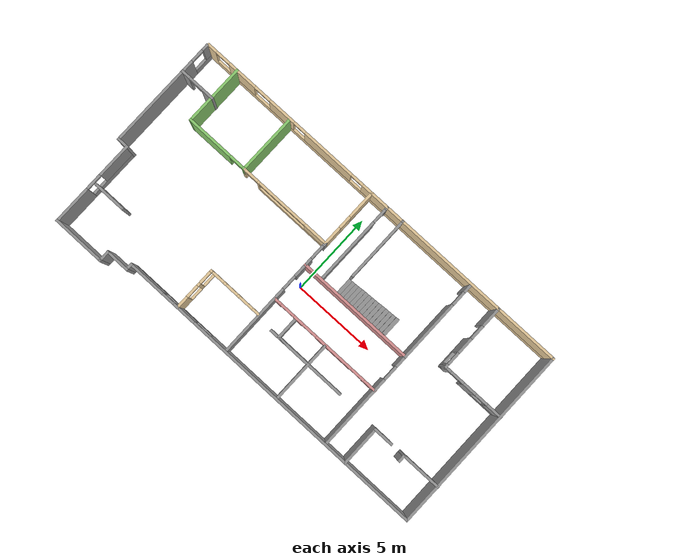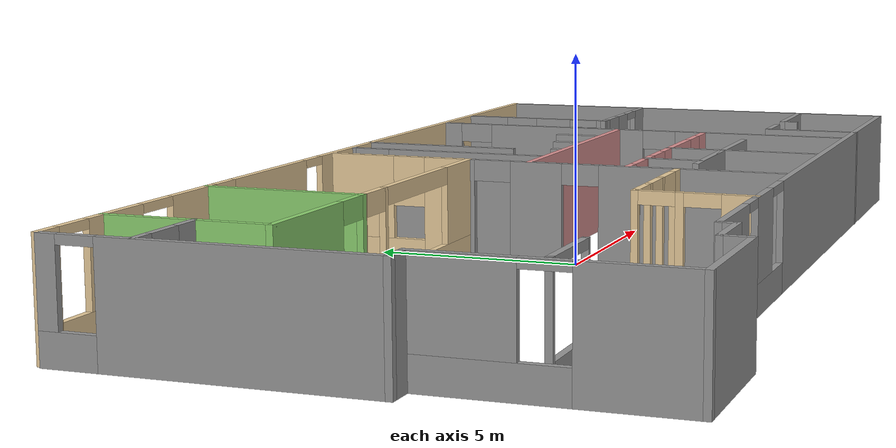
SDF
<?xml version='1.0'?>
<sdf version='1.6'>
  <model name='dunder_mifflin_scranton_full'>
    <pose frame=''>-0.003881 -0.031915 0 0 -0 0</pose>
    <link name='Stairs_0'>
      <visual name='Stairs_0_Visual_0'>
        <pose frame=''>1.73013 1.63779 0.083333 0 -0 1.5708</pose>
        <geometry>
          <box>
            <size>1.12038 0.229766 0.166667</size>
          </box>
        </geometry>
        <material>
          <script>
            <uri>file://media/materials/scripts/gazebo.material</uri>
            <name>Gazebo/Grey</name>
          </script>
          <ambient>1 1 1 1</ambient>
        </material>
        <meta>
          <layer>0</layer>
        </meta>
      </visual>
      <collision name='Stairs_0_Collision_0'>
        <geometry>
          <box>
            <size>1.12038 0.229766 0.166667</size>
          </box>
        </geometry>
        <pose frame=''>1.73013 1.63779 0.083333 0 -0 1.5708</pose>
      </collision>
      <visual name='Stairs_0_Visual_1'>
        <pose frame=''>1.9599 1.63779 0.25 0 -0 1.5708</pose>
        <geometry>
          <box>
            <size>1.12038 0.229766 0.166667</size>
          </box>
        </geometry>
        <material>
          <script>
            <uri>file://media/materials/scripts/gazebo.material</uri>
            <name>Gazebo/Grey</name>
          </script>
          <ambient>1 1 1 1</ambient>
        </material>
        <meta>
          <layer>0</layer>
        </meta>
      </visual>
      <collision name='Stairs_0_Collision_1'>
        <geometry>
          <box>
            <size>1.12038 0.229766 0.166667</size>
          </box>
        </geometry>
        <pose frame=''>1.9599 1.63779 0.25 0 -0 1.5708</pose>
      </collision>
      <visual name='Stairs_0_Visual_2'>
        <pose frame=''>2.18967 1.63779 0.416667 0 -0 1.5708</pose>
        <geometry>
          <box>
            <size>1.12038 0.229766 0.166667</size>
          </box>
        </geometry>
        <material>
          <script>
            <uri>file://media/materials/scripts/gazebo.material</uri>
            <name>Gazebo/Grey</name>
          </script>
          <ambient>1 1 1 1</ambient>
        </material>
        <meta>
          <layer>0</layer>
        </meta>
      </visual>
      <collision name='Stairs_0_Collision_2'>
        <geometry>
          <box>
            <size>1.12038 0.229766 0.166667</size>
          </box>
        </geometry>
        <pose frame=''>2.18967 1.63779 0.416667 0 -0 1.5708</pose>
      </collision>
      <visual name='Stairs_0_Visual_3'>
        <pose frame=''>2.41944 1.63779 0.583333 0 -0 1.5708</pose>
        <geometry>
          <box>
            <size>1.12038 0.229766 0.166667</size>
          </box>
        </geometry>
        <material>
          <script>
            <uri>file://media/materials/scripts/gazebo.material</uri>
            <name>Gazebo/Grey</name>
          </script>
          <ambient>1 1 1 1</ambient>
        </material>
        <meta>
          <layer>0</layer>
        </meta>
      </visual>
      <collision name='Stairs_0_Collision_3'>
        <geometry>
          <box>
            <size>1.12038 0.229766 0.166667</size>
          </box>
        </geometry>
        <pose frame=''>2.41944 1.63779 0.583333 0 -0 1.5708</pose>
      </collision>
      <visual name='Stairs_0_Visual_4'>
        <pose frame=''>2.6492 1.63779 0.75 0 -0 1.5708</pose>
        <geometry>
          <box>
            <size>1.12038 0.229766 0.166667</size>
          </box>
        </geometry>
        <material>
          <script>
            <uri>file://media/materials/scripts/gazebo.material</uri>
            <name>Gazebo/Grey</name>
          </script>
          <ambient>1 1 1 1</ambient>
        </material>
        <meta>
          <layer>0</layer>
        </meta>
      </visual>
      <collision name='Stairs_0_Collision_4'>
        <geometry>
          <box>
            <size>1.12038 0.229766 0.166667</size>
          </box>
        </geometry>
        <pose frame=''>2.6492 1.63779 0.75 0 -0 1.5708</pose>
      </collision>
      <visual name='Stairs_0_Visual_5'>
        <pose frame=''>2.87897 1.63779 0.916667 0 -0 1.5708</pose>
        <geometry>
          <box>
            <size>1.12038 0.229766 0.166667</size>
          </box>
        </geometry>
        <material>
          <script>
            <uri>file://media/materials/scripts/gazebo.material</uri>
            <name>Gazebo/Grey</name>
          </script>
          <ambient>1 1 1 1</ambient>
        </material>
        <meta>
          <layer>0</layer>
        </meta>
      </visual>
      <collision name='Stairs_0_Collision_5'>
        <geometry>
          <box>
            <size>1.12038 0.229766 0.166667</size>
          </box>
        </geometry>
        <pose frame=''>2.87897 1.63779 0.916667 0 -0 1.5708</pose>
      </collision>
      <visual name='Stairs_0_Visual_6'>
        <pose frame=''>3.10873 1.63779 1.08333 0 -0 1.5708</pose>
        <geometry>
          <box>
            <size>1.12038 0.229766 0.166667</size>
          </box>
        </geometry>
        <material>
          <script>
            <uri>file://media/materials/scripts/gazebo.material</uri>
            <name>Gazebo/Grey</name>
          </script>
          <ambient>1 1 1 1</ambient>
        </material>
        <meta>
          <layer>0</layer>
        </meta>
      </visual>
      <collision name='Stairs_0_Collision_6'>
        <geometry>
          <box>
            <size>1.12038 0.229766 0.166667</size>
          </box>
        </geometry>
        <pose frame=''>3.10873 1.63779 1.08333 0 -0 1.5708</pose>
      </collision>
      <visual name='Stairs_0_Visual_7'>
        <pose frame=''>3.3385 1.63779 1.25 0 -0 1.5708</pose>
        <geometry>
          <box>
            <size>1.12038 0.229766 0.166667</size>
          </box>
        </geometry>
        <material>
          <script>
            <uri>file://media/materials/scripts/gazebo.material</uri>
            <name>Gazebo/Grey</name>
          </script>
          <ambient>1 1 1 1</ambient>
        </material>
        <meta>
          <layer>0</layer>
        </meta>
      </visual>
      <collision name='Stairs_0_Collision_7'>
        <geometry>
          <box>
            <size>1.12038 0.229766 0.166667</size>
          </box>
        </geometry>
        <pose frame=''>3.3385 1.63779 1.25 0 -0 1.5708</pose>
      </collision>
      <visual name='Stairs_0_Visual_8'>
        <pose frame=''>3.56827 1.63779 1.41667 0 -0 1.5708</pose>
        <geometry>
          <box>
            <size>1.12038 0.229766 0.166667</size>
          </box>
        </geometry>
        <material>
          <script>
            <uri>file://media/materials/scripts/gazebo.material</uri>
            <name>Gazebo/Grey</name>
          </script>
          <ambient>1 1 1 1</ambient>
        </material>
        <meta>
          <layer>0</layer>
        </meta>
      </visual>
      <collision name='Stairs_0_Collision_8'>
        <geometry>
          <box>
            <size>1.12038 0.229766 0.166667</size>
          </box>
        </geometry>
        <pose frame=''>3.56827 1.63779 1.41667 0 -0 1.5708</pose>
      </collision>
      <visual name='Stairs_0_Visual_9'>
        <pose frame=''>3.79803 1.63779 1.58333 0 -0 1.5708</pose>
        <geometry>
          <box>
            <size>1.12038 0.229766 0.166667</size>
          </box>
        </geometry>
        <material>
          <script>
            <uri>file://media/materials/scripts/gazebo.material</uri>
            <name>Gazebo/Grey</name>
          </script>
          <ambient>1 1 1 1</ambient>
        </material>
        <meta>
          <layer>0</layer>
        </meta>
      </visual>
      <collision name='Stairs_0_Collision_9'>
        <geometry>
          <box>
            <size>1.12038 0.229766 0.166667</size>
          </box>
        </geometry>
        <pose frame=''>3.79803 1.63779 1.58333 0 -0 1.5708</pose>
      </collision>
      <visual name='Stairs_0_Visual_10'>
        <pose frame=''>4.0278 1.63779 1.75 0 -0 1.5708</pose>
        <geometry>
          <box>
            <size>1.12038 0.229766 0.166667</size>
          </box>
        </geometry>
        <material>
          <script>
            <uri>file://media/materials/scripts/gazebo.material</uri>
            <name>Gazebo/Grey</name>
          </script>
          <ambient>1 1 1 1</ambient>
        </material>
        <meta>
          <layer>0</layer>
        </meta>
      </visual>
      <collision name='Stairs_0_Collision_10'>
        <geometry>
          <box>
            <size>1.12038 0.229766 0.166667</size>
          </box>
        </geometry>
        <pose frame=''>4.0278 1.63779 1.75 0 -0 1.5708</pose>
      </collision>
      <visual name='Stairs_0_Visual_11'>
        <pose frame=''>4.25757 1.63779 1.91667 0 -0 1.5708</pose>
        <geometry>
          <box>
            <size>1.12038 0.229766 0.166667</size>
          </box>
        </geometry>
        <material>
          <script>
            <uri>file://media/materials/scripts/gazebo.material</uri>
            <name>Gazebo/Grey</name>
          </script>
          <ambient>1 1 1 1</ambient>
        </material>
        <meta>
          <layer>0</layer>
        </meta>
      </visual>
      <collision name='Stairs_0_Collision_11'>
        <geometry>
          <box>
            <size>1.12038 0.229766 0.166667</size>
          </box>
        </geometry>
        <pose frame=''>4.25757 1.63779 1.91667 0 -0 1.5708</pose>
      </collision>
      <visual name='Stairs_0_Visual_12'>
        <pose frame=''>4.48733 1.63779 2.08333 0 -0 1.5708</pose>
        <geometry>
          <box>
            <size>1.12038 0.229766 0.166667</size>
          </box>
        </geometry>
        <material>
          <script>
            <uri>file://media/materials/scripts/gazebo.material</uri>
            <name>Gazebo/Grey</name>
          </script>
          <ambient>1 1 1 1</ambient>
        </material>
        <meta>
          <layer>0</layer>
        </meta>
      </visual>
      <collision name='Stairs_0_Collision_12'>
        <geometry>
          <box>
            <size>1.12038 0.229766 0.166667</size>
          </box>
        </geometry>
        <pose frame=''>4.48733 1.63779 2.08333 0 -0 1.5708</pose>
      </collision>
      <visual name='Stairs_0_Visual_13'>
        <pose frame=''>4.7171 1.63779 2.25 0 -0 1.5708</pose>
        <geometry>
          <box>
            <size>1.12038 0.229766 0.166667</size>
          </box>
        </geometry>
        <material>
          <script>
            <uri>file://media/materials/scripts/gazebo.material</uri>
            <name>Gazebo/Grey</name>
          </script>
          <ambient>1 1 1 1</ambient>
        </material>
        <meta>
          <layer>0</layer>
        </meta>
      </visual>
      <collision name='Stairs_0_Collision_13'>
        <geometry>
          <box>
            <size>1.12038 0.229766 0.166667</size>
          </box>
        </geometry>
        <pose frame=''>4.7171 1.63779 2.25 0 -0 1.5708</pose>
      </collision>
      <visual name='Stairs_0_Visual_14'>
        <pose frame=''>4.94687 1.63779 2.41667 0 -0 1.5708</pose>
        <geometry>
          <box>
            <size>1.12038 0.229766 0.166667</size>
          </box>
        </geometry>
        <material>
          <script>
            <uri>file://media/materials/scripts/gazebo.material</uri>
            <name>Gazebo/Grey</name>
          </script>
          <ambient>1 1 1 1</ambient>
        </material>
        <meta>
          <layer>0</layer>
        </meta>
      </visual>
      <collision name='Stairs_0_Collision_14'>
        <geometry>
          <box>
            <size>1.12038 0.229766 0.166667</size>
          </box>
        </geometry>
        <pose frame=''>4.94687 1.63779 2.41667 0 -0 1.5708</pose>
      </collision>
    </link>
    <link name='Wall_10'>
      <collision name='Wall_10_Collision'>
        <geometry>
          <box>
            <size>1.5 0.15 2.5</size>
          </box>
        </geometry>
        <pose frame=''>0 0 1.25 0 -0 0</pose>
      </collision>
      <visual name='Wall_10_Visual'>
        <pose frame=''>0 0 1.25 0 -0 0</pose>
        <geometry>
          <box>
            <size>1.5 0.15 2.5</size>
          </box>
        </geometry>
        <material>
          <script>
            <uri>file://media/materials/scripts/gazebo.material</uri>
            <name>Gazebo/Grey</name>
          </script>
          <ambient>1 1 1 1</ambient>
        </material>
        <meta>
          <layer>0</layer>
        </meta>
      </visual>
      <pose frame=''>-7.95712 -5.55 0 0 -0 3.14159</pose>
    </link>
    <link name='Wall_11'>
      <collision name='Wall_11_Collision'>
        <geometry>
          <box>
            <size>0.75 0.15 2.5</size>
          </box>
        </geometry>
        <pose frame=''>0 0 1.25 0 -0 0</pose>
      </collision>
      <visual name='Wall_11_Visual'>
        <pose frame=''>0 0 1.25 0 -0 0</pose>
        <geometry>
          <box>
            <size>0.75 0.15 2.5</size>
          </box>
        </geometry>
        <material>
          <script>
            <uri>file://media/materials/scripts/gazebo.material</uri>
            <name>Gazebo/Grey</name>
          </script>
          <ambient>1 1 1 1</ambient>
        </material>
        <meta>
          <layer>0</layer>
        </meta>
      </visual>
      <pose frame=''>-8.63212 -5.85 0 0 -0 -1.5708</pose>
    </link>
    <link name='Wall_12'>
      <collision name='Wall_12_Collision'>
        <geometry>
          <box>
            <size>3.25 0.15 2.5</size>
          </box>
        </geometry>
        <pose frame=''>0 0 1.25 0 -0 0</pose>
      </collision>
      <visual name='Wall_12_Visual'>
        <pose frame=''>0 0 1.25 0 -0 0</pose>
        <geometry>
          <box>
            <size>3.25 0.15 2.5</size>
          </box>
        </geometry>
        <material>
          <script>
            <uri>file://media/materials/scripts/gazebo.material</uri>
            <name>Gazebo/Grey</name>
          </script>
          <ambient>1 1 1 1</ambient>
        </material>
        <meta>
          <layer>0</layer>
        </meta>
      </visual>
      <pose frame=''>-10.1821 -6.15 0 0 -0 3.14159</pose>
    </link>
    <link name='Wall_13'>
      <pose frame=''>-11.7321 -3.475 0 0 -0 1.5708</pose>
      <visual name='Wall_13_Visual_0'>
        <pose frame=''>-1.56118 0 1.25 0 -0 0</pose>
        <geometry>
          <box>
            <size>2.37764 0.15 2.5</size>
          </box>
        </geometry>
        <material>
          <script>
            <uri>file://media/materials/scripts/gazebo.material</uri>
            <name>Gazebo/Grey</name>
          </script>
          <ambient>1 1 1 1</ambient>
        </material>
        <meta>
          <layer>0</layer>
        </meta>
      </visual>
      <collision name='Wall_13_Collision_0'>
        <geometry>
          <box>
            <size>2.37764 0.15 2.5</size>
          </box>
        </geometry>
        <pose frame=''>-1.56118 0 1.25 0 -0 0</pose>
      </collision>
      <visual name='Wall_13_Visual_1'>
        <pose frame=''>1.18882 0 0.35 0 -0 0</pose>
        <geometry>
          <box>
            <size>3.12236 0.15 0.7</size>
          </box>
        </geometry>
        <material>
          <script>
            <uri>file://media/materials/scripts/gazebo.material</uri>
            <name>Gazebo/Grey</name>
          </script>
          <ambient>1 1 1 1</ambient>
        </material>
        <meta>
          <layer>0</layer>
        </meta>
      </visual>
      <collision name='Wall_13_Collision_1'>
        <geometry>
          <box>
            <size>3.12236 0.15 0.7</size>
          </box>
        </geometry>
        <pose frame=''>1.18882 0 0.35 0 -0 0</pose>
      </collision>
      <visual name='Wall_13_Visual_2'>
        <pose frame=''>1.67832 0 1.6 0 -0 0</pose>
        <geometry>
          <box>
            <size>2.14336 0.15 1.8</size>
          </box>
        </geometry>
        <material>
          <script>
            <uri>file://media/materials/scripts/gazebo.material</uri>
            <name>Gazebo/Grey</name>
          </script>
          <ambient>1 1 1 1</ambient>
        </material>
        <meta>
          <layer>0</layer>
        </meta>
      </visual>
      <collision name='Wall_13_Collision_2'>
        <geometry>
          <box>
            <size>2.14336 0.15 1.8</size>
          </box>
        </geometry>
        <pose frame=''>1.67832 0 1.6 0 -0 0</pose>
      </collision>
      <visual name='Wall_13_Visual_3'>
        <pose frame=''>0.117145 0 2.4 0 -0 0</pose>
        <geometry>
          <box>
            <size>0.979 0.15 0.2</size>
          </box>
        </geometry>
        <material>
          <script>
            <uri>file://media/materials/scripts/gazebo.material</uri>
            <name>Gazebo/Grey</name>
          </script>
          <ambient>1 1 1 1</ambient>
        </material>
        <meta>
          <layer>0</layer>
        </meta>
      </visual>
      <collision name='Wall_13_Collision_3'>
        <geometry>
          <box>
            <size>0.979 0.15 0.2</size>
          </box>
        </geometry>
        <pose frame=''>0.117145 0 2.4 0 -0 0</pose>
      </collision>
    </link>
    <link name='Wall_14'>
      <collision name='Wall_14_Collision'>
        <geometry>
          <box>
            <size>0.75 0.15 2.5</size>
          </box>
        </geometry>
        <pose frame=''>0 0 1.25 0 -0 0</pose>
      </collision>
      <visual name='Wall_14_Visual'>
        <pose frame=''>0 0 1.25 0 -0 0</pose>
        <geometry>
          <box>
            <size>0.75 0.15 2.5</size>
          </box>
        </geometry>
        <material>
          <script>
            <uri>file://media/materials/scripts/gazebo.material</uri>
            <name>Gazebo/Grey</name>
          </script>
          <ambient>1 1 1 1</ambient>
        </material>
        <meta>
          <layer>0</layer>
        </meta>
      </visual>
      <pose frame=''>-12.0321 -0.8 0 0 -0 3.14159</pose>
    </link>
    <link name='Wall_15'>
      <pose frame=''>-12.3321 2.625 0 0 -0 1.5708</pose>
      <visual name='Wall_15_Visual_0'>
        <pose frame=''>-0.612803 0 1.25 0 -0 0</pose>
        <geometry>
          <box>
            <size>5.7744 0.15 2.5</size>
          </box>
        </geometry>
        <material>
          <script>
            <uri>file://media/materials/scripts/gazebo.material</uri>
            <name>Gazebo/Grey</name>
          </script>
          <ambient>1 1 1 1</ambient>
        </material>
        <meta>
          <layer>0</layer>
        </meta>
      </visual>
      <collision name='Wall_15_Collision_0'>
        <geometry>
          <box>
            <size>5.7744 0.15 2.5</size>
          </box>
        </geometry>
        <pose frame=''>-0.612803 0 1.25 0 -0 0</pose>
      </collision>
      <visual name='Wall_15_Visual_1'>
        <pose frame=''>2.8872 0 0.35 0 -0 0</pose>
        <geometry>
          <box>
            <size>1.22561 0.15 0.7</size>
          </box>
        </geometry>
        <material>
          <script>
            <uri>file://media/materials/scripts/gazebo.material</uri>
            <name>Gazebo/Grey</name>
          </script>
          <ambient>1 1 1 1</ambient>
        </material>
        <meta>
          <layer>0</layer>
        </meta>
      </visual>
      <collision name='Wall_15_Collision_1'>
        <geometry>
          <box>
            <size>1.22561 0.15 0.7</size>
          </box>
        </geometry>
        <pose frame=''>2.8872 0 0.35 0 -0 0</pose>
      </collision>
      <visual name='Wall_15_Visual_2'>
        <pose frame=''>3.2872 0 1.6 0 -0 0</pose>
        <geometry>
          <box>
            <size>0.425605 0.15 1.8</size>
          </box>
        </geometry>
        <material>
          <script>
            <uri>file://media/materials/scripts/gazebo.material</uri>
            <name>Gazebo/Grey</name>
          </script>
          <ambient>1 1 1 1</ambient>
        </material>
        <meta>
          <layer>0</layer>
        </meta>
      </visual>
      <collision name='Wall_15_Collision_2'>
        <geometry>
          <box>
            <size>0.425605 0.15 1.8</size>
          </box>
        </geometry>
        <pose frame=''>3.2872 0 1.6 0 -0 0</pose>
      </collision>
      <visual name='Wall_15_Visual_3'>
        <pose frame=''>2.6744 0 2.4 0 -0 0</pose>
        <geometry>
          <box>
            <size>0.8 0.15 0.2</size>
          </box>
        </geometry>
        <material>
          <script>
            <uri>file://media/materials/scripts/gazebo.material</uri>
            <name>Gazebo/Grey</name>
          </script>
          <ambient>1 1 1 1</ambient>
        </material>
        <meta>
          <layer>0</layer>
        </meta>
      </visual>
      <collision name='Wall_15_Collision_3'>
        <geometry>
          <box>
            <size>0.8 0.15 0.2</size>
          </box>
        </geometry>
        <pose frame=''>2.6744 0 2.4 0 -0 0</pose>
      </collision>
    </link>
    <link name='Wall_19'>
      <collision name='Wall_19_Collision'>
        <geometry>
          <box>
            <size>3.75 0.15 2.5</size>
          </box>
        </geometry>
        <pose frame=''>0 0 1.25 0 -0 0</pose>
      </collision>
      <visual name='Wall_19_Visual'>
        <pose frame=''>0 0 1.25 0 -0 0</pose>
        <geometry>
          <box>
            <size>3.75 0.15 2.5</size>
          </box>
        </geometry>
        <material>
          <script>
            <uri>file://media/materials/scripts/gazebo.material</uri>
            <name>Gazebo/Grey</name>
          </script>
          <ambient>0.556863 0.823529 0.443137 1</ambient>
        </material>
        <meta>
          <layer>0</layer>
        </meta>
      </visual>
      <pose frame=''>-10.2322 4.33925 0 0 -0 -1.5708</pose>
    </link>
    <link name='Wall_20'>
      <pose frame=''>-8.30724 2.53925 0 0 -0 0</pose>
      <visual name='Wall_20_Visual_0'>
        <pose frame=''>-0.536103 0 1.25 0 -0 0</pose>
        <geometry>
          <box>
            <size>2.92779 0.15 2.5</size>
          </box>
        </geometry>
        <material>
          <script>
            <uri>file://media/materials/scripts/gazebo.material</uri>
            <name>Gazebo/Grey</name>
          </script>
          <ambient>0.556863 0.823529 0.443137 1</ambient>
        </material>
        <meta>
          <layer>0</layer>
        </meta>
      </visual>
      <collision name='Wall_20_Collision_0'>
        <geometry>
          <box>
            <size>2.92779 0.15 2.5</size>
          </box>
        </geometry>
        <pose frame=''>-0.536103 0 1.25 0 -0 0</pose>
      </collision>
      <visual name='Wall_20_Visual_1'>
        <pose frame=''>1.9139 0 1.25 0 -0 0</pose>
        <geometry>
          <box>
            <size>0.172206 0.15 2.5</size>
          </box>
        </geometry>
        <material>
          <script>
            <uri>file://media/materials/scripts/gazebo.material</uri>
            <name>Gazebo/Grey</name>
          </script>
          <ambient>0.556863 0.823529 0.443137 1</ambient>
        </material>
        <meta>
          <layer>0</layer>
        </meta>
      </visual>
      <collision name='Wall_20_Collision_1'>
        <geometry>
          <box>
            <size>0.172206 0.15 2.5</size>
          </box>
        </geometry>
        <pose frame=''>1.9139 0 1.25 0 -0 0</pose>
      </collision>
      <visual name='Wall_20_Visual_2'>
        <pose frame=''>1.37779 0 2.25 0 -0 0</pose>
        <geometry>
          <box>
            <size>0.9 0.15 0.5</size>
          </box>
        </geometry>
        <material>
          <script>
            <uri>file://media/materials/scripts/gazebo.material</uri>
            <name>Gazebo/Grey</name>
          </script>
          <ambient>0.556863 0.823529 0.443137 1</ambient>
        </material>
        <meta>
          <layer>0</layer>
        </meta>
      </visual>
      <collision name='Wall_20_Collision_2'>
        <geometry>
          <box>
            <size>0.9 0.15 0.5</size>
          </box>
        </geometry>
        <pose frame=''>1.37779 0 2.25 0 -0 0</pose>
      </collision>
    </link>
    <link name='Wall_21'>
      <collision name='Wall_21_Collision'>
        <geometry>
          <box>
            <size>3.75 0.15 2.5</size>
          </box>
        </geometry>
        <pose frame=''>0 0 1.25 0 -0 0</pose>
      </collision>
      <visual name='Wall_21_Visual'>
        <pose frame=''>0 0 1.25 0 -0 0</pose>
        <geometry>
          <box>
            <size>3.75 0.15 2.5</size>
          </box>
        </geometry>
        <material>
          <script>
            <uri>file://media/materials/scripts/gazebo.material</uri>
            <name>Gazebo/Grey</name>
          </script>
          <ambient>0.556863 0.823529 0.443137 1</ambient>
        </material>
        <meta>
          <layer>0</layer>
        </meta>
      </visual>
      <pose frame=''>-6.38225 4.33925 0 0 -0 1.5708</pose>
    </link>
    <link name='Wall_23'>
      <pose frame=''>-3.45724 2.53925 0 0 -0 0</pose>
      <visual name='Wall_23_Visual_0'>
        <pose frame=''>-2.91414 0 1.25 0 -0 0</pose>
        <geometry>
          <box>
            <size>0.171718 0.15 2.5</size>
          </box>
        </geometry>
        <material>
          <script>
            <uri>file://media/materials/scripts/gazebo.material</uri>
            <name>Gazebo/Grey</name>
          </script>
          <ambient>0.921569 0.807843 0.615686 1</ambient>
        </material>
        <meta>
          <layer>0</layer>
        </meta>
      </visual>
      <collision name='Wall_23_Collision_0'>
        <geometry>
          <box>
            <size>0.171718 0.15 2.5</size>
          </box>
        </geometry>
        <pose frame=''>-2.91414 0 1.25 0 -0 0</pose>
      </collision>
      <visual name='Wall_23_Visual_1'>
        <pose frame=''>-1.86179 0 1.25 0 -0 0</pose>
        <geometry>
          <box>
            <size>0.132993 0.15 2.5</size>
          </box>
        </geometry>
        <material>
          <script>
            <uri>file://media/materials/scripts/gazebo.material</uri>
            <name>Gazebo/Grey</name>
          </script>
          <ambient>0.921569 0.807843 0.615686 1</ambient>
        </material>
        <meta>
          <layer>0</layer>
        </meta>
      </visual>
      <collision name='Wall_23_Collision_1'>
        <geometry>
          <box>
            <size>0.132993 0.15 2.5</size>
          </box>
        </geometry>
        <pose frame=''>-1.86179 0 1.25 0 -0 0</pose>
      </collision>
      <visual name='Wall_23_Visual_2'>
        <pose frame=''>0.602356 0 0.35 0 -0 0</pose>
        <geometry>
          <box>
            <size>4.79529 0.15 0.7</size>
          </box>
        </geometry>
        <material>
          <script>
            <uri>file://media/materials/scripts/gazebo.material</uri>
            <name>Gazebo/Grey</name>
          </script>
          <ambient>0.921569 0.807843 0.615686 1</ambient>
        </material>
        <meta>
          <layer>0</layer>
        </meta>
      </visual>
      <collision name='Wall_23_Collision_2'>
        <geometry>
          <box>
            <size>4.79529 0.15 0.7</size>
          </box>
        </geometry>
        <pose frame=''>0.602356 0 0.35 0 -0 0</pose>
      </collision>
      <visual name='Wall_23_Visual_3'>
        <pose frame=''>2.22271 0 1.6 0 -0 0</pose>
        <geometry>
          <box>
            <size>1.55459 0.15 1.8</size>
          </box>
        </geometry>
        <material>
          <script>
            <uri>file://media/materials/scripts/gazebo.material</uri>
            <name>Gazebo/Grey</name>
          </script>
          <ambient>0.921569 0.807843 0.615686 1</ambient>
        </material>
        <meta>
          <layer>0</layer>
        </meta>
      </visual>
      <collision name='Wall_23_Collision_3'>
        <geometry>
          <box>
            <size>1.55459 0.15 1.8</size>
          </box>
        </geometry>
        <pose frame=''>2.22271 0 1.6 0 -0 0</pose>
      </collision>
      <visual name='Wall_23_Visual_4'>
        <pose frame=''>-2.37828 0 2.25 0 -0 0</pose>
        <geometry>
          <box>
            <size>0.9 0.15 0.5</size>
          </box>
        </geometry>
        <material>
          <script>
            <uri>file://media/materials/scripts/gazebo.material</uri>
            <name>Gazebo/Grey</name>
          </script>
          <ambient>0.921569 0.807843 0.615686 1</ambient>
        </material>
        <meta>
          <layer>0</layer>
        </meta>
      </visual>
      <collision name='Wall_23_Collision_4'>
        <geometry>
          <box>
            <size>0.9 0.15 0.5</size>
          </box>
        </geometry>
        <pose frame=''>-2.37828 0 2.25 0 -0 0</pose>
      </collision>
      <visual name='Wall_23_Visual_5'>
        <pose frame=''>-0.174937 0 2.3 0 -0 0</pose>
        <geometry>
          <box>
            <size>3.2407 0.15 0.4</size>
          </box>
        </geometry>
        <material>
          <script>
            <uri>file://media/materials/scripts/gazebo.material</uri>
            <name>Gazebo/Grey</name>
          </script>
          <ambient>0.921569 0.807843 0.615686 1</ambient>
        </material>
        <meta>
          <layer>0</layer>
        </meta>
      </visual>
      <collision name='Wall_23_Collision_5'>
        <geometry>
          <box>
            <size>3.2407 0.15 0.4</size>
          </box>
        </geometry>
        <pose frame=''>-0.174937 0 2.3 0 -0 0</pose>
      </collision>
    </link>
    <link name='Wall_24'>
      <pose frame=''>-0.532245 4.33925 0 0 -0 1.5708</pose>
      <visual name='Wall_24_Visual_0'>
        <pose frame=''>-1.28185 0 1.25 0 -0 0</pose>
        <geometry>
          <box>
            <size>1.1863 0.15 2.5</size>
          </box>
        </geometry>
        <material>
          <script>
            <uri>file://media/materials/scripts/gazebo.material</uri>
            <name>Gazebo/Grey</name>
          </script>
          <ambient>0.921569 0.807843 0.615686 1</ambient>
        </material>
        <meta>
          <layer>0</layer>
        </meta>
      </visual>
      <collision name='Wall_24_Collision_0'>
        <geometry>
          <box>
            <size>1.1863 0.15 2.5</size>
          </box>
        </geometry>
        <pose frame=''>-1.28185 0 1.25 0 -0 0</pose>
      </collision>
      <visual name='Wall_24_Visual_1'>
        <pose frame=''>0.59315 0 0.25 0 -0 0</pose>
        <geometry>
          <box>
            <size>2.5637 0.15 0.5</size>
          </box>
        </geometry>
        <material>
          <script>
            <uri>file://media/materials/scripts/gazebo.material</uri>
            <name>Gazebo/Grey</name>
          </script>
          <ambient>0.921569 0.807843 0.615686 1</ambient>
        </material>
        <meta>
          <layer>0</layer>
        </meta>
      </visual>
      <collision name='Wall_24_Collision_1'>
        <geometry>
          <box>
            <size>2.5637 0.15 0.5</size>
          </box>
        </geometry>
        <pose frame=''>0.59315 0 0.25 0 -0 0</pose>
      </collision>
      <visual name='Wall_24_Visual_2'>
        <pose frame=''>0.99315 0 1.5 0 -0 0</pose>
        <geometry>
          <box>
            <size>1.7637 0.15 2</size>
          </box>
        </geometry>
        <material>
          <script>
            <uri>file://media/materials/scripts/gazebo.material</uri>
            <name>Gazebo/Grey</name>
          </script>
          <ambient>0.921569 0.807843 0.615686 1</ambient>
        </material>
        <meta>
          <layer>0</layer>
        </meta>
      </visual>
      <collision name='Wall_24_Collision_2'>
        <geometry>
          <box>
            <size>1.7637 0.15 2</size>
          </box>
        </geometry>
        <pose frame=''>0.99315 0 1.5 0 -0 0</pose>
      </collision>
      <visual name='Wall_24_Visual_3'>
        <pose frame=''>-0.288699 0 1.9 0 -0 0</pose>
        <geometry>
          <box>
            <size>0.8 0.15 1.2</size>
          </box>
        </geometry>
        <material>
          <script>
            <uri>file://media/materials/scripts/gazebo.material</uri>
            <name>Gazebo/Grey</name>
          </script>
          <ambient>0.921569 0.807843 0.615686 1</ambient>
        </material>
        <meta>
          <layer>0</layer>
        </meta>
      </visual>
      <collision name='Wall_24_Collision_3'>
        <geometry>
          <box>
            <size>0.8 0.15 1.2</size>
          </box>
        </geometry>
        <pose frame=''>-0.288699 0 1.9 0 -0 0</pose>
      </collision>
    </link>
    <link name='Wall_26'>
      <pose frame=''>-0.532245 -1.26075 0 0 -0 -1.5708</pose>
      <visual name='Wall_26_Visual_0'>
        <pose frame=''>-3.74743 0 1.25 0 -0 0</pose>
        <geometry>
          <box>
            <size>0.255133 0.15 2.5</size>
          </box>
        </geometry>
        <material>
          <script>
            <uri>file://media/materials/scripts/gazebo.material</uri>
            <name>Gazebo/Grey</name>
          </script>
          <ambient>1 1 1 1</ambient>
        </material>
        <meta>
          <layer>0</layer>
        </meta>
      </visual>
      <collision name='Wall_26_Collision_0'>
        <geometry>
          <box>
            <size>0.255133 0.15 2.5</size>
          </box>
        </geometry>
        <pose frame=''>-3.74743 0 1.25 0 -0 0</pose>
      </collision>
      <visual name='Wall_26_Visual_1'>
        <pose frame=''>-2.08102 0 1.25 0 -0 0</pose>
        <geometry>
          <box>
            <size>1.27769 0.15 2.5</size>
          </box>
        </geometry>
        <material>
          <script>
            <uri>file://media/materials/scripts/gazebo.material</uri>
            <name>Gazebo/Grey</name>
          </script>
          <ambient>1 1 1 1</ambient>
        </material>
        <meta>
          <layer>0</layer>
        </meta>
      </visual>
      <collision name='Wall_26_Collision_1'>
        <geometry>
          <box>
            <size>1.27769 0.15 2.5</size>
          </box>
        </geometry>
        <pose frame=''>-2.08102 0 1.25 0 -0 0</pose>
      </collision>
      <visual name='Wall_26_Visual_2'>
        <pose frame=''>1.66641 0 1.25 0 -0 0</pose>
        <geometry>
          <box>
            <size>4.41718 0.15 2.5</size>
          </box>
        </geometry>
        <material>
          <script>
            <uri>file://media/materials/scripts/gazebo.material</uri>
            <name>Gazebo/Grey</name>
          </script>
          <ambient>1 1 1 1</ambient>
        </material>
        <meta>
          <layer>0</layer>
        </meta>
      </visual>
      <collision name='Wall_26_Collision_2'>
        <geometry>
          <box>
            <size>4.41718 0.15 2.5</size>
          </box>
        </geometry>
        <pose frame=''>1.66641 0 1.25 0 -0 0</pose>
      </collision>
      <visual name='Wall_26_Visual_3'>
        <pose frame=''>-3.16987 0 2.25 0 -0 0</pose>
        <geometry>
          <box>
            <size>0.9 0.15 0.5</size>
          </box>
        </geometry>
        <material>
          <script>
            <uri>file://media/materials/scripts/gazebo.material</uri>
            <name>Gazebo/Grey</name>
          </script>
          <ambient>1 1 1 1</ambient>
        </material>
        <meta>
          <layer>0</layer>
        </meta>
      </visual>
      <collision name='Wall_26_Collision_3'>
        <geometry>
          <box>
            <size>0.9 0.15 0.5</size>
          </box>
        </geometry>
        <pose frame=''>-3.16987 0 2.25 0 -0 0</pose>
      </collision>
      <visual name='Wall_26_Visual_4'>
        <pose frame=''>-0.992175 0 2.25 0 -0 0</pose>
        <geometry>
          <box>
            <size>0.9 0.15 0.5</size>
          </box>
        </geometry>
        <material>
          <script>
            <uri>file://media/materials/scripts/gazebo.material</uri>
            <name>Gazebo/Grey</name>
          </script>
          <ambient>1 1 1 1</ambient>
        </material>
        <meta>
          <layer>0</layer>
        </meta>
      </visual>
      <collision name='Wall_26_Collision_4'>
        <geometry>
          <box>
            <size>0.9 0.15 0.5</size>
          </box>
        </geometry>
        <pose frame=''>-0.992175 0 2.25 0 -0 0</pose>
      </collision>
    </link>
    <link name='Wall_28'>
      <pose frame=''>-3.95331 -3.89431 0 0 -0 1.5708</pose>
      <visual name='Wall_28_Visual_0'>
        <pose frame=''>-0.969422 0 1.25 0 -0 0</pose>
        <geometry>
          <box>
            <size>0.811156 0.15 2.5</size>
          </box>
        </geometry>
        <material>
          <script>
            <uri>file://media/materials/scripts/gazebo.material</uri>
            <name>Gazebo/Grey</name>
          </script>
          <ambient>0.921569 0.807843 0.615686 1</ambient>
        </material>
        <meta>
          <layer>0</layer>
        </meta>
      </visual>
      <collision name='Wall_28_Collision_0'>
        <geometry>
          <box>
            <size>0.811156 0.15 2.5</size>
          </box>
        </geometry>
        <pose frame=''>-0.969422 0 1.25 0 -0 0</pose>
      </collision>
      <visual name='Wall_28_Visual_1'>
        <pose frame=''>0.405578 0 0.1 0 -0 0</pose>
        <geometry>
          <box>
            <size>1.93884 0.15 0.2</size>
          </box>
        </geometry>
        <material>
          <script>
            <uri>file://media/materials/scripts/gazebo.material</uri>
            <name>Gazebo/Grey</name>
          </script>
          <ambient>0.921569 0.807843 0.615686 1</ambient>
        </material>
        <meta>
          <layer>0</layer>
        </meta>
      </visual>
      <collision name='Wall_28_Collision_1'>
        <geometry>
          <box>
            <size>1.93884 0.15 0.2</size>
          </box>
        </geometry>
        <pose frame=''>0.405578 0 0.1 0 -0 0</pose>
      </collision>
      <visual name='Wall_28_Visual_2'>
        <pose frame=''>0.328659 0 1.35 0 -0 0</pose>
        <geometry>
          <box>
            <size>0.185005 0.15 2.3</size>
          </box>
        </geometry>
        <material>
          <script>
            <uri>file://media/materials/scripts/gazebo.material</uri>
            <name>Gazebo/Grey</name>
          </script>
          <ambient>0.921569 0.807843 0.615686 1</ambient>
        </material>
        <meta>
          <layer>0</layer>
        </meta>
      </visual>
      <collision name='Wall_28_Collision_2'>
        <geometry>
          <box>
            <size>0.185005 0.15 2.3</size>
          </box>
        </geometry>
        <pose frame=''>0.328659 0 1.35 0 -0 0</pose>
      </collision>
      <visual name='Wall_28_Visual_3'>
        <pose frame=''>1.29808 0 1.35 0 -0 0</pose>
        <geometry>
          <box>
            <size>0.153838 0.15 2.3</size>
          </box>
        </geometry>
        <material>
          <script>
            <uri>file://media/materials/scripts/gazebo.material</uri>
            <name>Gazebo/Grey</name>
          </script>
          <ambient>0.921569 0.807843 0.615686 1</ambient>
        </material>
        <meta>
          <layer>0</layer>
        </meta>
      </visual>
      <collision name='Wall_28_Collision_3'>
        <geometry>
          <box>
            <size>0.153838 0.15 2.3</size>
          </box>
        </geometry>
        <pose frame=''>1.29808 0 1.35 0 -0 0</pose>
      </collision>
      <visual name='Wall_28_Visual_4'>
        <pose frame=''>-0.163844 0 2.35 0 -0 0</pose>
        <geometry>
          <box>
            <size>0.8 0.15 0.3</size>
          </box>
        </geometry>
        <material>
          <script>
            <uri>file://media/materials/scripts/gazebo.material</uri>
            <name>Gazebo/Grey</name>
          </script>
          <ambient>0.921569 0.807843 0.615686 1</ambient>
        </material>
        <meta>
          <layer>0</layer>
        </meta>
      </visual>
      <collision name='Wall_28_Collision_4'>
        <geometry>
          <box>
            <size>0.8 0.15 0.3</size>
          </box>
        </geometry>
        <pose frame=''>-0.163844 0 2.35 0 -0 0</pose>
      </collision>
      <visual name='Wall_28_Visual_5'>
        <pose frame=''>0.821162 0 2.35 0 -0 0</pose>
        <geometry>
          <box>
            <size>0.8 0.15 0.3</size>
          </box>
        </geometry>
        <material>
          <script>
            <uri>file://media/materials/scripts/gazebo.material</uri>
            <name>Gazebo/Grey</name>
          </script>
          <ambient>0.921569 0.807843 0.615686 1</ambient>
        </material>
        <meta>
          <layer>0</layer>
        </meta>
      </visual>
      <collision name='Wall_28_Collision_5'>
        <geometry>
          <box>
            <size>0.8 0.15 0.3</size>
          </box>
        </geometry>
        <pose frame=''>0.821162 0 2.35 0 -0 0</pose>
      </collision>
    </link>
    <link name='Wall_29'>
      <pose frame=''>-2.27831 -2.59431 0 0 -0 0</pose>
      <visual name='Wall_29_Visual_0'>
        <pose frame=''>-1.66131 0 1.25 0 -0 0</pose>
        <geometry>
          <box>
            <size>0.177371 0.15 2.5</size>
          </box>
        </geometry>
        <material>
          <script>
            <uri>file://media/materials/scripts/gazebo.material</uri>
            <name>Gazebo/Grey</name>
          </script>
          <ambient>0.921569 0.807843 0.615686 1</ambient>
        </material>
        <meta>
          <layer>0</layer>
        </meta>
      </visual>
      <collision name='Wall_29_Collision_0'>
        <geometry>
          <box>
            <size>0.177371 0.15 2.5</size>
          </box>
        </geometry>
        <pose frame=''>-1.66131 0 1.25 0 -0 0</pose>
      </collision>
      <visual name='Wall_29_Visual_1'>
        <pose frame=''>1.50358 0 1.25 0 -0 0</pose>
        <geometry>
          <box>
            <size>0.492835 0.15 2.5</size>
          </box>
        </geometry>
        <material>
          <script>
            <uri>file://media/materials/scripts/gazebo.material</uri>
            <name>Gazebo/Grey</name>
          </script>
          <ambient>0.921569 0.807843 0.615686 1</ambient>
        </material>
        <meta>
          <layer>0</layer>
        </meta>
      </visual>
      <collision name='Wall_29_Collision_1'>
        <geometry>
          <box>
            <size>0.492835 0.15 2.5</size>
          </box>
        </geometry>
        <pose frame=''>1.50358 0 1.25 0 -0 0</pose>
      </collision>
      <visual name='Wall_29_Visual_2'>
        <pose frame=''>-0.607732 0 0.1 0 -0 0</pose>
        <geometry>
          <box>
            <size>1.92979 0.15 0.2</size>
          </box>
        </geometry>
        <material>
          <script>
            <uri>file://media/materials/scripts/gazebo.material</uri>
            <name>Gazebo/Grey</name>
          </script>
          <ambient>0.921569 0.807843 0.615686 1</ambient>
        </material>
        <meta>
          <layer>0</layer>
        </meta>
      </visual>
      <collision name='Wall_29_Collision_2'>
        <geometry>
          <box>
            <size>1.92979 0.15 0.2</size>
          </box>
        </geometry>
        <pose frame=''>-0.607732 0 0.1 0 -0 0</pose>
      </collision>
      <visual name='Wall_29_Visual_3'>
        <pose frame=''>-0.685949 0 1.35 0 -0 0</pose>
        <geometry>
          <box>
            <size>0.17336 0.15 2.3</size>
          </box>
        </geometry>
        <material>
          <script>
            <uri>file://media/materials/scripts/gazebo.material</uri>
            <name>Gazebo/Grey</name>
          </script>
          <ambient>0.921569 0.807843 0.615686 1</ambient>
        </material>
        <meta>
          <layer>0</layer>
        </meta>
      </visual>
      <collision name='Wall_29_Collision_3'>
        <geometry>
          <box>
            <size>0.17336 0.15 2.3</size>
          </box>
        </geometry>
        <pose frame=''>-0.685949 0 1.35 0 -0 0</pose>
      </collision>
      <visual name='Wall_29_Visual_4'>
        <pose frame=''>0.278948 0 1.35 0 -0 0</pose>
        <geometry>
          <box>
            <size>0.156434 0.15 2.3</size>
          </box>
        </geometry>
        <material>
          <script>
            <uri>file://media/materials/scripts/gazebo.material</uri>
            <name>Gazebo/Grey</name>
          </script>
          <ambient>0.921569 0.807843 0.615686 1</ambient>
        </material>
        <meta>
          <layer>0</layer>
        </meta>
      </visual>
      <collision name='Wall_29_Collision_4'>
        <geometry>
          <box>
            <size>0.156434 0.15 2.3</size>
          </box>
        </geometry>
        <pose frame=''>0.278948 0 1.35 0 -0 0</pose>
      </collision>
      <visual name='Wall_29_Visual_5'>
        <pose frame=''>0.807165 0 2.25 0 -0 0</pose>
        <geometry>
          <box>
            <size>0.9 0.15 0.5</size>
          </box>
        </geometry>
        <material>
          <script>
            <uri>file://media/materials/scripts/gazebo.material</uri>
            <name>Gazebo/Grey</name>
          </script>
          <ambient>0.921569 0.807843 0.615686 1</ambient>
        </material>
        <meta>
          <layer>0</layer>
        </meta>
      </visual>
      <collision name='Wall_29_Collision_5'>
        <geometry>
          <box>
            <size>0.9 0.15 0.5</size>
          </box>
        </geometry>
        <pose frame=''>0.807165 0 2.25 0 -0 0</pose>
      </collision>
      <visual name='Wall_29_Visual_6'>
        <pose frame=''>-1.17263 0 2.35 0 -0 0</pose>
        <geometry>
          <box>
            <size>0.8 0.15 0.3</size>
          </box>
        </geometry>
        <material>
          <script>
            <uri>file://media/materials/scripts/gazebo.material</uri>
            <name>Gazebo/Grey</name>
          </script>
          <ambient>0.921569 0.807843 0.615686 1</ambient>
        </material>
        <meta>
          <layer>0</layer>
        </meta>
      </visual>
      <collision name='Wall_29_Collision_6'>
        <geometry>
          <box>
            <size>0.8 0.15 0.3</size>
          </box>
        </geometry>
        <pose frame=''>-1.17263 0 2.35 0 -0 0</pose>
      </collision>
      <visual name='Wall_29_Visual_7'>
        <pose frame=''>-0.199269 0 2.35 0 -0 0</pose>
        <geometry>
          <box>
            <size>0.8 0.15 0.3</size>
          </box>
        </geometry>
        <material>
          <script>
            <uri>file://media/materials/scripts/gazebo.material</uri>
            <name>Gazebo/Grey</name>
          </script>
          <ambient>0.921569 0.807843 0.615686 1</ambient>
        </material>
        <meta>
          <layer>0</layer>
        </meta>
      </visual>
      <collision name='Wall_29_Collision_7'>
        <geometry>
          <box>
            <size>0.8 0.15 0.3</size>
          </box>
        </geometry>
        <pose frame=''>-0.199269 0 2.35 0 -0 0</pose>
      </collision>
    </link>
    <link name='Wall_31'>
      <collision name='Wall_31_Collision'>
        <geometry>
          <box>
            <size>7.25 0.15 2.5</size>
          </box>
        </geometry>
        <pose frame=''>0 0 1.25 0 -0 0</pose>
      </collision>
      <visual name='Wall_31_Visual'>
        <pose frame=''>0 0 1.25 0 -0 0</pose>
        <geometry>
          <box>
            <size>7.25 0.15 2.5</size>
          </box>
        </geometry>
        <material>
          <script>
            <uri>file://media/materials/scripts/gazebo.material</uri>
            <name>Gazebo/Grey</name>
          </script>
          <ambient>0.866667 0.584314 0.584314 1</ambient>
        </material>
        <meta>
          <layer>0</layer>
        </meta>
      </visual>
      <pose frame=''>3.02474 0.997169 0 0 -0 0</pose>
    </link>
    <link name='Wall_32'>
      <pose frame=''>6.57474 -2.05283 0 0 -0 -1.5708</pose>
      <visual name='Wall_32_Visual_0'>
        <pose frame=''>-2.72846 0 1.25 0 -0 0</pose>
        <geometry>
          <box>
            <size>0.793072 0.15 2.5</size>
          </box>
        </geometry>
        <material>
          <script>
            <uri>file://media/materials/scripts/gazebo.material</uri>
            <name>Gazebo/Grey</name>
          </script>
          <ambient>1 1 1 1</ambient>
        </material>
        <meta>
          <layer>0</layer>
        </meta>
      </visual>
      <collision name='Wall_32_Collision_0'>
        <geometry>
          <box>
            <size>0.793072 0.15 2.5</size>
          </box>
        </geometry>
        <pose frame=''>-2.72846 0 1.25 0 -0 0</pose>
      </collision>
      <visual name='Wall_32_Visual_1'>
        <pose frame=''>0.846536 0 1.25 0 -0 0</pose>
        <geometry>
          <box>
            <size>4.55693 0.15 2.5</size>
          </box>
        </geometry>
        <material>
          <script>
            <uri>file://media/materials/scripts/gazebo.material</uri>
            <name>Gazebo/Grey</name>
          </script>
          <ambient>1 1 1 1</ambient>
        </material>
        <meta>
          <layer>0</layer>
        </meta>
      </visual>
      <collision name='Wall_32_Collision_1'>
        <geometry>
          <box>
            <size>4.55693 0.15 2.5</size>
          </box>
        </geometry>
        <pose frame=''>0.846536 0 1.25 0 -0 0</pose>
      </collision>
      <visual name='Wall_32_Visual_2'>
        <pose frame=''>-1.88193 0 2.25 0 -0 0</pose>
        <geometry>
          <box>
            <size>0.9 0.15 0.5</size>
          </box>
        </geometry>
        <material>
          <script>
            <uri>file://media/materials/scripts/gazebo.material</uri>
            <name>Gazebo/Grey</name>
          </script>
          <ambient>1 1 1 1</ambient>
        </material>
        <meta>
          <layer>0</layer>
        </meta>
      </visual>
      <collision name='Wall_32_Collision_2'>
        <geometry>
          <box>
            <size>0.9 0.15 0.5</size>
          </box>
        </geometry>
        <pose frame=''>-1.88193 0 2.25 0 -0 0</pose>
      </collision>
    </link>
    <link name='Wall_34'>
      <pose frame=''>3.04223 -1.39897 0 0 -0 0</pose>
      <visual name='Wall_34_Visual_0'>
        <pose frame=''>-3.36018 0 1.25 0 -0 0</pose>
        <geometry>
          <box>
            <size>0.529643 0.15 2.5</size>
          </box>
        </geometry>
        <material>
          <script>
            <uri>file://media/materials/scripts/gazebo.material</uri>
            <name>Gazebo/Grey</name>
          </script>
          <ambient>0.866667 0.584314 0.584314 1</ambient>
        </material>
        <meta>
          <layer>0</layer>
        </meta>
      </visual>
      <collision name='Wall_34_Collision_0'>
        <geometry>
          <box>
            <size>0.529643 0.15 2.5</size>
          </box>
        </geometry>
        <pose frame=''>-3.36018 0 1.25 0 -0 0</pose>
      </collision>
      <visual name='Wall_34_Visual_1'>
        <pose frame=''>-1.86211 0 1.25 0 -0 0</pose>
        <geometry>
          <box>
            <size>0.666501 0.15 2.5</size>
          </box>
        </geometry>
        <material>
          <script>
            <uri>file://media/materials/scripts/gazebo.material</uri>
            <name>Gazebo/Grey</name>
          </script>
          <ambient>0.866667 0.584314 0.584314 1</ambient>
        </material>
        <meta>
          <layer>0</layer>
        </meta>
      </visual>
      <collision name='Wall_34_Collision_1'>
        <geometry>
          <box>
            <size>0.666501 0.15 2.5</size>
          </box>
        </geometry>
        <pose frame=''>-1.86211 0 1.25 0 -0 0</pose>
      </collision>
      <visual name='Wall_34_Visual_2'>
        <pose frame=''>0.624524 0 1.25 0 -0 0</pose>
        <geometry>
          <box>
            <size>2.50676 0.15 2.5</size>
          </box>
        </geometry>
        <material>
          <script>
            <uri>file://media/materials/scripts/gazebo.material</uri>
            <name>Gazebo/Grey</name>
          </script>
          <ambient>0.866667 0.584314 0.584314 1</ambient>
        </material>
        <meta>
          <layer>0</layer>
        </meta>
      </visual>
      <collision name='Wall_34_Collision_2'>
        <geometry>
          <box>
            <size>2.50676 0.15 2.5</size>
          </box>
        </geometry>
        <pose frame=''>0.624524 0 1.25 0 -0 0</pose>
      </collision>
      <visual name='Wall_34_Visual_3'>
        <pose frame=''>3.20145 0 1.25 0 -0 0</pose>
        <geometry>
          <box>
            <size>0.847096 0.15 2.5</size>
          </box>
        </geometry>
        <material>
          <script>
            <uri>file://media/materials/scripts/gazebo.material</uri>
            <name>Gazebo/Grey</name>
          </script>
          <ambient>0.866667 0.584314 0.584314 1</ambient>
        </material>
        <meta>
          <layer>0</layer>
        </meta>
      </visual>
      <collision name='Wall_34_Collision_3'>
        <geometry>
          <box>
            <size>0.847096 0.15 2.5</size>
          </box>
        </geometry>
        <pose frame=''>3.20145 0 1.25 0 -0 0</pose>
      </collision>
      <visual name='Wall_34_Visual_4'>
        <pose frame=''>-2.64536 0 2.25 0 -0 0</pose>
        <geometry>
          <box>
            <size>0.9 0.15 0.5</size>
          </box>
        </geometry>
        <material>
          <script>
            <uri>file://media/materials/scripts/gazebo.material</uri>
            <name>Gazebo/Grey</name>
          </script>
          <ambient>0.866667 0.584314 0.584314 1</ambient>
        </material>
        <meta>
          <layer>0</layer>
        </meta>
      </visual>
      <collision name='Wall_34_Collision_4'>
        <geometry>
          <box>
            <size>0.9 0.15 0.5</size>
          </box>
        </geometry>
        <pose frame=''>-2.64536 0 2.25 0 -0 0</pose>
      </collision>
      <visual name='Wall_34_Visual_5'>
        <pose frame=''>-1.07886 0 2.25 0 -0 0</pose>
        <geometry>
          <box>
            <size>0.9 0.15 0.5</size>
          </box>
        </geometry>
        <material>
          <script>
            <uri>file://media/materials/scripts/gazebo.material</uri>
            <name>Gazebo/Grey</name>
          </script>
          <ambient>0.866667 0.584314 0.584314 1</ambient>
        </material>
        <meta>
          <layer>0</layer>
        </meta>
      </visual>
      <collision name='Wall_34_Collision_5'>
        <geometry>
          <box>
            <size>0.9 0.15 0.5</size>
          </box>
        </geometry>
        <pose frame=''>-1.07886 0 2.25 0 -0 0</pose>
      </collision>
      <visual name='Wall_34_Visual_6'>
        <pose frame=''>2.3279 0 2.25 0 -0 0</pose>
        <geometry>
          <box>
            <size>0.9 0.15 0.5</size>
          </box>
        </geometry>
        <material>
          <script>
            <uri>file://media/materials/scripts/gazebo.material</uri>
            <name>Gazebo/Grey</name>
          </script>
          <ambient>0.866667 0.584314 0.584314 1</ambient>
        </material>
        <meta>
          <layer>0</layer>
        </meta>
      </visual>
      <collision name='Wall_34_Collision_6'>
        <geometry>
          <box>
            <size>0.9 0.15 0.5</size>
          </box>
        </geometry>
        <pose frame=''>2.3279 0 2.25 0 -0 0</pose>
      </collision>
    </link>
    <link name='Wall_36'>
      <pose frame=''>6.57474 3.54717 0 0 -0 1.5708</pose>
      <visual name='Wall_36_Visual_0'>
        <pose frame=''>-0.74582 0 1.25 0 -0 0</pose>
        <geometry>
          <box>
            <size>3.75836 0.15 2.5</size>
          </box>
        </geometry>
        <material>
          <script>
            <uri>file://media/materials/scripts/gazebo.material</uri>
            <name>Gazebo/Grey</name>
          </script>
          <ambient>1 1 1 1</ambient>
        </material>
        <meta>
          <layer>0</layer>
        </meta>
      </visual>
      <collision name='Wall_36_Collision_0'>
        <geometry>
          <box>
            <size>3.75836 0.15 2.5</size>
          </box>
        </geometry>
        <pose frame=''>-0.74582 0 1.25 0 -0 0</pose>
      </collision>
      <visual name='Wall_36_Visual_1'>
        <pose frame=''>2.32918 0 1.25 0 -0 0</pose>
        <geometry>
          <box>
            <size>0.591641 0.15 2.5</size>
          </box>
        </geometry>
        <material>
          <script>
            <uri>file://media/materials/scripts/gazebo.material</uri>
            <name>Gazebo/Grey</name>
          </script>
          <ambient>1 1 1 1</ambient>
        </material>
        <meta>
          <layer>0</layer>
        </meta>
      </visual>
      <collision name='Wall_36_Collision_1'>
        <geometry>
          <box>
            <size>0.591641 0.15 2.5</size>
          </box>
        </geometry>
        <pose frame=''>2.32918 0 1.25 0 -0 0</pose>
      </collision>
      <visual name='Wall_36_Visual_2'>
        <pose frame=''>1.58336 0 2.25 0 -0 0</pose>
        <geometry>
          <box>
            <size>0.9 0.15 0.5</size>
          </box>
        </geometry>
        <material>
          <script>
            <uri>file://media/materials/scripts/gazebo.material</uri>
            <name>Gazebo/Grey</name>
          </script>
          <ambient>1 1 1 1</ambient>
        </material>
        <meta>
          <layer>0</layer>
        </meta>
      </visual>
      <collision name='Wall_36_Collision_2'>
        <geometry>
          <box>
            <size>0.9 0.15 0.5</size>
          </box>
        </geometry>
        <pose frame=''>1.58336 0 2.25 0 -0 0</pose>
      </collision>
    </link>
    <link name='Wall_38'>
      <pose frame=''>8.48212 4.07176 0 0 -0 -1.5708</pose>
      <visual name='Wall_38_Visual_0'>
        <pose frame=''>-1.4899 0 1.25 0 -0 0</pose>
        <geometry>
          <box>
            <size>1.27021 0.15 2.5</size>
          </box>
        </geometry>
        <material>
          <script>
            <uri>file://media/materials/scripts/gazebo.material</uri>
            <name>Gazebo/Grey</name>
          </script>
          <ambient>0.423529 0.423529 0.423529 1</ambient>
        </material>
        <meta>
          <layer>0</layer>
        </meta>
      </visual>
      <collision name='Wall_38_Collision_0'>
        <geometry>
          <box>
            <size>1.27021 0.15 2.5</size>
          </box>
        </geometry>
        <pose frame=''>-1.4899 0 1.25 0 -0 0</pose>
      </collision>
      <visual name='Wall_38_Visual_1'>
        <pose frame=''>0.548931 0 1.25 0 -0 0</pose>
        <geometry>
          <box>
            <size>1.00745 0.15 2.5</size>
          </box>
        </geometry>
        <material>
          <script>
            <uri>file://media/materials/scripts/gazebo.material</uri>
            <name>Gazebo/Grey</name>
          </script>
          <ambient>0.423529 0.423529 0.423529 1</ambient>
        </material>
        <meta>
          <layer>0</layer>
        </meta>
      </visual>
      <collision name='Wall_38_Collision_1'>
        <geometry>
          <box>
            <size>1.00745 0.15 2.5</size>
          </box>
        </geometry>
        <pose frame=''>0.548931 0 1.25 0 -0 0</pose>
      </collision>
      <visual name='Wall_38_Visual_2'>
        <pose frame=''>1.58883 0 0.35 0 -0 0</pose>
        <geometry>
          <box>
            <size>1.07234 0.15 0.7</size>
          </box>
        </geometry>
        <material>
          <script>
            <uri>file://media/materials/scripts/gazebo.material</uri>
            <name>Gazebo/Grey</name>
          </script>
          <ambient>0.423529 0.423529 0.423529 1</ambient>
        </material>
        <meta>
          <layer>0</layer>
        </meta>
      </visual>
      <collision name='Wall_38_Collision_2'>
        <geometry>
          <box>
            <size>1.07234 0.15 0.7</size>
          </box>
        </geometry>
        <pose frame=''>1.58883 0 0.35 0 -0 0</pose>
      </collision>
      <visual name='Wall_38_Visual_3'>
        <pose frame=''>1.98883 0 1.6 0 -0 0</pose>
        <geometry>
          <box>
            <size>0.272344 0.15 1.8</size>
          </box>
        </geometry>
        <material>
          <script>
            <uri>file://media/materials/scripts/gazebo.material</uri>
            <name>Gazebo/Grey</name>
          </script>
          <ambient>0.423529 0.423529 0.423529 1</ambient>
        </material>
        <meta>
          <layer>0</layer>
        </meta>
      </visual>
      <collision name='Wall_38_Collision_3'>
        <geometry>
          <box>
            <size>0.272344 0.15 1.8</size>
          </box>
        </geometry>
        <pose frame=''>1.98883 0 1.6 0 -0 0</pose>
      </collision>
      <visual name='Wall_38_Visual_4'>
        <pose frame=''>-0.404794 0 2.25 0 -0 0</pose>
        <geometry>
          <box>
            <size>0.9 0.15 0.5</size>
          </box>
        </geometry>
        <material>
          <script>
            <uri>file://media/materials/scripts/gazebo.material</uri>
            <name>Gazebo/Grey</name>
          </script>
          <ambient>0.423529 0.423529 0.423529 1</ambient>
        </material>
        <meta>
          <layer>0</layer>
        </meta>
      </visual>
      <collision name='Wall_38_Collision_4'>
        <geometry>
          <box>
            <size>0.9 0.15 0.5</size>
          </box>
        </geometry>
        <pose frame=''>-0.404794 0 2.25 0 -0 0</pose>
      </collision>
      <visual name='Wall_38_Visual_5'>
        <pose frame=''>1.45266 0 2.4 0 -0 0</pose>
        <geometry>
          <box>
            <size>0.8 0.15 0.2</size>
          </box>
        </geometry>
        <material>
          <script>
            <uri>file://media/materials/scripts/gazebo.material</uri>
            <name>Gazebo/Grey</name>
          </script>
          <ambient>0.423529 0.423529 0.423529 1</ambient>
        </material>
        <meta>
          <layer>0</layer>
        </meta>
      </visual>
      <collision name='Wall_38_Collision_5'>
        <geometry>
          <box>
            <size>0.8 0.15 0.2</size>
          </box>
        </geometry>
        <pose frame=''>1.45266 0 2.4 0 -0 0</pose>
      </collision>
    </link>
    <link name='Wall_39'>
      <pose frame=''>10.4071 2.02176 0 0 -0 0</pose>
      <visual name='Wall_39_Visual_0'>
        <pose frame=''>-1.78157 0 1.25 0 -0 0</pose>
        <geometry>
          <box>
            <size>0.436869 0.15 2.5</size>
          </box>
        </geometry>
        <material>
          <script>
            <uri>file://media/materials/scripts/gazebo.material</uri>
            <name>Gazebo/Grey</name>
          </script>
          <ambient>0.423529 0.423529 0.423529 1</ambient>
        </material>
        <meta>
          <layer>0</layer>
        </meta>
      </visual>
      <collision name='Wall_39_Collision_0'>
        <geometry>
          <box>
            <size>0.436869 0.15 2.5</size>
          </box>
        </geometry>
        <pose frame=''>-1.78157 0 1.25 0 -0 0</pose>
      </collision>
      <visual name='Wall_39_Visual_1'>
        <pose frame=''>-0.241405 0 1.25 0 -0 0</pose>
        <geometry>
          <box>
            <size>0.843451 0.15 2.5</size>
          </box>
        </geometry>
        <material>
          <script>
            <uri>file://media/materials/scripts/gazebo.material</uri>
            <name>Gazebo/Grey</name>
          </script>
          <ambient>0.423529 0.423529 0.423529 1</ambient>
        </material>
        <meta>
          <layer>0</layer>
        </meta>
      </visual>
      <collision name='Wall_39_Collision_1'>
        <geometry>
          <box>
            <size>0.843451 0.15 2.5</size>
          </box>
        </geometry>
        <pose frame=''>-0.241405 0 1.25 0 -0 0</pose>
      </collision>
      <visual name='Wall_39_Visual_2'>
        <pose frame=''>1.09016 0 0.35 0 -0 0</pose>
        <geometry>
          <box>
            <size>1.81968 0.15 0.7</size>
          </box>
        </geometry>
        <material>
          <script>
            <uri>file://media/materials/scripts/gazebo.material</uri>
            <name>Gazebo/Grey</name>
          </script>
          <ambient>0.423529 0.423529 0.423529 1</ambient>
        </material>
        <meta>
          <layer>0</layer>
        </meta>
      </visual>
      <collision name='Wall_39_Collision_2'>
        <geometry>
          <box>
            <size>1.81968 0.15 0.7</size>
          </box>
        </geometry>
        <pose frame=''>1.09016 0 0.35 0 -0 0</pose>
      </collision>
      <visual name='Wall_39_Visual_3'>
        <pose frame=''>1.49016 0 1.6 0 -0 0</pose>
        <geometry>
          <box>
            <size>1.01968 0.15 1.8</size>
          </box>
        </geometry>
        <material>
          <script>
            <uri>file://media/materials/scripts/gazebo.material</uri>
            <name>Gazebo/Grey</name>
          </script>
          <ambient>0.423529 0.423529 0.423529 1</ambient>
        </material>
        <meta>
          <layer>0</layer>
        </meta>
      </visual>
      <collision name='Wall_39_Collision_3'>
        <geometry>
          <box>
            <size>1.01968 0.15 1.8</size>
          </box>
        </geometry>
        <pose frame=''>1.49016 0 1.6 0 -0 0</pose>
      </collision>
      <visual name='Wall_39_Visual_4'>
        <pose frame=''>-1.11313 0 2.25 0 -0 0</pose>
        <geometry>
          <box>
            <size>0.9 0.15 0.5</size>
          </box>
        </geometry>
        <material>
          <script>
            <uri>file://media/materials/scripts/gazebo.material</uri>
            <name>Gazebo/Grey</name>
          </script>
          <ambient>0.423529 0.423529 0.423529 1</ambient>
        </material>
        <meta>
          <layer>0</layer>
        </meta>
      </visual>
      <collision name='Wall_39_Collision_4'>
        <geometry>
          <box>
            <size>0.9 0.15 0.5</size>
          </box>
        </geometry>
        <pose frame=''>-1.11313 0 2.25 0 -0 0</pose>
      </collision>
      <visual name='Wall_39_Visual_5'>
        <pose frame=''>0.58032 0 2.4 0 -0 0</pose>
        <geometry>
          <box>
            <size>0.8 0.15 0.2</size>
          </box>
        </geometry>
        <material>
          <script>
            <uri>file://media/materials/scripts/gazebo.material</uri>
            <name>Gazebo/Grey</name>
          </script>
          <ambient>0.423529 0.423529 0.423529 1</ambient>
        </material>
        <meta>
          <layer>0</layer>
        </meta>
      </visual>
      <collision name='Wall_39_Collision_5'>
        <geometry>
          <box>
            <size>0.8 0.15 0.2</size>
          </box>
        </geometry>
        <pose frame=''>0.58032 0 2.4 0 -0 0</pose>
      </collision>
    </link>
    <link name='Wall_41'>
      <collision name='Wall_41_Collision'>
        <geometry>
          <box>
            <size>2.5 0.15 2.5</size>
          </box>
        </geometry>
        <pose frame=''>0 0 1.25 0 -0 0</pose>
      </collision>
      <visual name='Wall_41_Visual'>
        <pose frame=''>0 0 1.25 0 -0 0</pose>
        <geometry>
          <box>
            <size>2.5 0.15 2.5</size>
          </box>
        </geometry>
        <material>
          <script>
            <uri>file://media/materials/scripts/gazebo.material</uri>
            <name>Gazebo/Grey</name>
          </script>
          <ambient>1 1 1 1</ambient>
        </material>
        <meta>
          <layer>0</layer>
        </meta>
      </visual>
      <pose frame=''>11.1549 -2.85065 0 0 -0 3.14159</pose>
    </link>
    <link name='Wall_42'>
      <collision name='Wall_42_Collision'>
        <geometry>
          <box>
            <size>0.5 0.15 2.5</size>
          </box>
        </geometry>
        <pose frame=''>0 0 1.25 0 -0 0</pose>
      </collision>
      <visual name='Wall_42_Visual'>
        <pose frame=''>0 0 1.25 0 -0 0</pose>
        <geometry>
          <box>
            <size>0.5 0.15 2.5</size>
          </box>
        </geometry>
        <material>
          <script>
            <uri>file://media/materials/scripts/gazebo.material</uri>
            <name>Gazebo/Grey</name>
          </script>
          <ambient>1 1 1 1</ambient>
        </material>
        <meta>
          <layer>0</layer>
        </meta>
      </visual>
      <pose frame=''>9.97994 -3.02564 0 0 -0 -1.5708</pose>
    </link>
    <link name='Wall_44'>
      <collision name='Wall_44_Collision'>
        <geometry>
          <box>
            <size>2.5 0.15 2.5</size>
          </box>
        </geometry>
        <pose frame=''>0 0 1.25 0 -0 0</pose>
      </collision>
      <visual name='Wall_44_Visual'>
        <pose frame=''>0 0 1.25 0 -0 0</pose>
        <geometry>
          <box>
            <size>2.5 0.15 2.5</size>
          </box>
        </geometry>
        <material>
          <script>
            <uri>file://media/materials/scripts/gazebo.material</uri>
            <name>Gazebo/Grey</name>
          </script>
          <ambient>1 1 1 1</ambient>
        </material>
        <meta>
          <layer>0</layer>
        </meta>
      </visual>
      <pose frame=''>7.97491 -4.0368 0 0 -0 1.5708</pose>
    </link>
    <link name='Wall_45'>
      <collision name='Wall_45_Collision'>
        <geometry>
          <box>
            <size>1.25 0.15 2.5</size>
          </box>
        </geometry>
        <pose frame=''>0 0 1.25 0 -0 0</pose>
      </collision>
      <visual name='Wall_45_Visual'>
        <pose frame=''>0 0 1.25 0 -0 0</pose>
        <geometry>
          <box>
            <size>1.25 0.15 2.5</size>
          </box>
        </geometry>
        <material>
          <script>
            <uri>file://media/materials/scripts/gazebo.material</uri>
            <name>Gazebo/Grey</name>
          </script>
          <ambient>1 1 1 1</ambient>
        </material>
        <meta>
          <layer>0</layer>
        </meta>
      </visual>
      <pose frame=''>8.52491 -2.8618 0 0 -0 0</pose>
    </link>
    <link name='Wall_55'>
      <collision name='Wall_55_Collision'>
        <geometry>
          <box>
            <size>1.5 0.15 2.5</size>
          </box>
        </geometry>
        <pose frame=''>0 0 1.25 0 -0 0</pose>
      </collision>
      <visual name='Wall_55_Visual'>
        <pose frame=''>0 0 1.25 0 -0 0</pose>
        <geometry>
          <box>
            <size>1.5 0.15 2.5</size>
          </box>
        </geometry>
        <material>
          <script>
            <uri>file://media/materials/scripts/gazebo.material</uri>
            <name>Gazebo/Grey</name>
          </script>
          <ambient>1 1 1 1</ambient>
        </material>
        <meta>
          <layer>0</layer>
        </meta>
      </visual>
      <pose frame=''>1.01387 -2.07397 0 0 -0 -1.5708</pose>
    </link>
    <link name='Wall_56'>
      <collision name='Wall_56_Collision'>
        <geometry>
          <box>
            <size>2.25 0.15 2.5</size>
          </box>
        </geometry>
        <pose frame=''>0 0 1.25 0 -0 0</pose>
      </collision>
      <visual name='Wall_56_Visual'>
        <pose frame=''>0 0 1.25 0 -0 0</pose>
        <geometry>
          <box>
            <size>2.25 0.15 2.5</size>
          </box>
        </geometry>
        <material>
          <script>
            <uri>file://media/materials/scripts/gazebo.material</uri>
            <name>Gazebo/Grey</name>
          </script>
          <ambient>1 1 1 1</ambient>
        </material>
        <meta>
          <layer>0</layer>
        </meta>
      </visual>
      <pose frame=''>2.06386 -2.74897 0 0 -0 0</pose>
    </link>
    <link name='Wall_57'>
      <collision name='Wall_57_Collision'>
        <geometry>
          <box>
            <size>2.5 0.15 2.5</size>
          </box>
        </geometry>
        <pose frame=''>0 0 1.25 0 -0 0</pose>
      </collision>
      <visual name='Wall_57_Visual'>
        <pose frame=''>0 0 1.25 0 -0 0</pose>
        <geometry>
          <box>
            <size>2.5 0.15 2.5</size>
          </box>
        </geometry>
        <material>
          <script>
            <uri>file://media/materials/scripts/gazebo.material</uri>
            <name>Gazebo/Grey</name>
          </script>
          <ambient>1 1 1 1</ambient>
        </material>
        <meta>
          <layer>0</layer>
        </meta>
      </visual>
      <pose frame=''>3.11387 -3.92397 0 0 -0 -1.5708</pose>
    </link>
    <link name='Wall_59'>
      <collision name='Wall_59_Collision'>
        <geometry>
          <box>
            <size>1.5 0.15 2.5</size>
          </box>
        </geometry>
        <pose frame=''>0 0 1.25 0 -0 0</pose>
      </collision>
      <visual name='Wall_59_Visual'>
        <pose frame=''>0 0 1.25 0 -0 0</pose>
        <geometry>
          <box>
            <size>1.5 0.15 2.5</size>
          </box>
        </geometry>
        <material>
          <script>
            <uri>file://media/materials/scripts/gazebo.material</uri>
            <name>Gazebo/Grey</name>
          </script>
          <ambient>1 1 1 1</ambient>
        </material>
        <meta>
          <layer>0</layer>
        </meta>
      </visual>
      <pose frame=''>3.11387 -2.07397 0 0 -0 1.5708</pose>
    </link>
    <link name='Wall_6'>
      <pose frame=''>0.017879 6.15 0 0 -0 0</pose>
      <visual name='Wall_6_Visual_0'>
        <pose frame=''>-12.0548 0 1.25 0 -0 0</pose>
        <geometry>
          <box>
            <size>0.640363 0.15 2.5</size>
          </box>
        </geometry>
        <material>
          <script>
            <uri>file://media/materials/scripts/gazebo.material</uri>
            <name>Gazebo/Grey</name>
          </script>
          <ambient>0.921569 0.807843 0.615686 1</ambient>
        </material>
        <meta>
          <layer>0</layer>
        </meta>
      </visual>
      <collision name='Wall_6_Collision_0'>
        <geometry>
          <box>
            <size>0.640363 0.15 2.5</size>
          </box>
        </geometry>
        <pose frame=''>-12.0548 0 1.25 0 -0 0</pose>
      </collision>
      <visual name='Wall_6_Visual_1'>
        <pose frame=''>0.320182 0 0.35 0 -0 0</pose>
        <geometry>
          <box>
            <size>24.1096 0.15 0.7</size>
          </box>
        </geometry>
        <material>
          <script>
            <uri>file://media/materials/scripts/gazebo.material</uri>
            <name>Gazebo/Grey</name>
          </script>
          <ambient>0.921569 0.807843 0.615686 1</ambient>
        </material>
        <meta>
          <layer>0</layer>
        </meta>
      </visual>
      <collision name='Wall_6_Collision_1'>
        <geometry>
          <box>
            <size>24.1096 0.15 0.7</size>
          </box>
        </geometry>
        <pose frame=''>0.320182 0 0.35 0 -0 0</pose>
      </collision>
      <visual name='Wall_6_Visual_2'>
        <pose frame=''>-9.87682 0 1.6 0 -0 0</pose>
        <geometry>
          <box>
            <size>1.84964 0.15 1.8</size>
          </box>
        </geometry>
        <material>
          <script>
            <uri>file://media/materials/scripts/gazebo.material</uri>
            <name>Gazebo/Grey</name>
          </script>
          <ambient>0.921569 0.807843 0.615686 1</ambient>
        </material>
        <meta>
          <layer>0</layer>
        </meta>
      </visual>
      <collision name='Wall_6_Collision_2'>
        <geometry>
          <box>
            <size>1.84964 0.15 1.8</size>
          </box>
        </geometry>
        <pose frame=''>-9.87682 0 1.6 0 -0 0</pose>
      </collision>
      <visual name='Wall_6_Visual_3'>
        <pose frame=''>-6.99137 0 1.6 0 -0 0</pose>
        <geometry>
          <box>
            <size>1.74331 0.15 1.8</size>
          </box>
        </geometry>
        <material>
          <script>
            <uri>file://media/materials/scripts/gazebo.material</uri>
            <name>Gazebo/Grey</name>
          </script>
          <ambient>0.921569 0.807843 0.615686 1</ambient>
        </material>
        <meta>
          <layer>0</layer>
        </meta>
      </visual>
      <collision name='Wall_6_Collision_3'>
        <geometry>
          <box>
            <size>1.74331 0.15 1.8</size>
          </box>
        </geometry>
        <pose frame=''>-6.99137 0 1.6 0 -0 0</pose>
      </collision>
      <visual name='Wall_6_Visual_4'>
        <pose frame=''>-3.6528 0 1.6 0 -0 0</pose>
        <geometry>
          <box>
            <size>3.33383 0.15 1.8</size>
          </box>
        </geometry>
        <material>
          <script>
            <uri>file://media/materials/scripts/gazebo.material</uri>
            <name>Gazebo/Grey</name>
          </script>
          <ambient>0.921569 0.807843 0.615686 1</ambient>
        </material>
        <meta>
          <layer>0</layer>
        </meta>
      </visual>
      <collision name='Wall_6_Collision_4'>
        <geometry>
          <box>
            <size>3.33383 0.15 1.8</size>
          </box>
        </geometry>
        <pose frame=''>-3.6528 0 1.6 0 -0 0</pose>
      </collision>
      <visual name='Wall_6_Visual_5'>
        <pose frame=''>5.59456 0 1.6 0 -0 0</pose>
        <geometry>
          <box>
            <size>13.5609 0.15 1.8</size>
          </box>
        </geometry>
        <material>
          <script>
            <uri>file://media/materials/scripts/gazebo.material</uri>
            <name>Gazebo/Grey</name>
          </script>
          <ambient>0.921569 0.807843 0.615686 1</ambient>
        </material>
        <meta>
          <layer>0</layer>
        </meta>
      </visual>
      <collision name='Wall_6_Collision_5'>
        <geometry>
          <box>
            <size>13.5609 0.15 1.8</size>
          </box>
        </geometry>
        <pose frame=''>5.59456 0 1.6 0 -0 0</pose>
      </collision>
      <visual name='Wall_6_Visual_6'>
        <pose frame=''>-11.2681 0 2.4 0 -0 0</pose>
        <geometry>
          <box>
            <size>0.933 0.15 0.2</size>
          </box>
        </geometry>
        <material>
          <script>
            <uri>file://media/materials/scripts/gazebo.material</uri>
            <name>Gazebo/Grey</name>
          </script>
          <ambient>0.921569 0.807843 0.615686 1</ambient>
        </material>
        <meta>
          <layer>0</layer>
        </meta>
      </visual>
      <collision name='Wall_6_Collision_6'>
        <geometry>
          <box>
            <size>0.933 0.15 0.2</size>
          </box>
        </geometry>
        <pose frame=''>-11.2681 0 2.4 0 -0 0</pose>
      </collision>
      <visual name='Wall_6_Visual_7'>
        <pose frame=''>-8.40751 0 2.4 0 -0 0</pose>
        <geometry>
          <box>
            <size>1.08897 0.15 0.2</size>
          </box>
        </geometry>
        <material>
          <script>
            <uri>file://media/materials/scripts/gazebo.material</uri>
            <name>Gazebo/Grey</name>
          </script>
          <ambient>0.921569 0.807843 0.615686 1</ambient>
        </material>
        <meta>
          <layer>0</layer>
        </meta>
      </visual>
      <collision name='Wall_6_Collision_7'>
        <geometry>
          <box>
            <size>1.08897 0.15 0.2</size>
          </box>
        </geometry>
        <pose frame=''>-8.40751 0 2.4 0 -0 0</pose>
      </collision>
      <visual name='Wall_6_Visual_8'>
        <pose frame=''>-5.71972 0 2.4 0 -0 0</pose>
        <geometry>
          <box>
            <size>0.8 0.15 0.2</size>
          </box>
        </geometry>
        <material>
          <script>
            <uri>file://media/materials/scripts/gazebo.material</uri>
            <name>Gazebo/Grey</name>
          </script>
          <ambient>0.921569 0.807843 0.615686 1</ambient>
        </material>
        <meta>
          <layer>0</layer>
        </meta>
      </visual>
      <collision name='Wall_6_Collision_8'>
        <geometry>
          <box>
            <size>0.8 0.15 0.2</size>
          </box>
        </geometry>
        <pose frame=''>-5.71972 0 2.4 0 -0 0</pose>
      </collision>
      <visual name='Wall_6_Visual_9'>
        <pose frame=''>-1.58589 0 2.4 0 -0 0</pose>
        <geometry>
          <box>
            <size>0.8 0.15 0.2</size>
          </box>
        </geometry>
        <material>
          <script>
            <uri>file://media/materials/scripts/gazebo.material</uri>
            <name>Gazebo/Grey</name>
          </script>
          <ambient>0.921569 0.807843 0.615686 1</ambient>
        </material>
        <meta>
          <layer>0</layer>
        </meta>
      </visual>
      <collision name='Wall_6_Collision_9'>
        <geometry>
          <box>
            <size>0.8 0.15 0.2</size>
          </box>
        </geometry>
        <pose frame=''>-1.58589 0 2.4 0 -0 0</pose>
      </collision>
    </link>
    <link name='Wall_62'>
      <collision name='Wall_62_Collision'>
        <geometry>
          <box>
            <size>5 0.15 2.5</size>
          </box>
        </geometry>
        <pose frame=''>0 0 1.25 0 -0 0</pose>
      </collision>
      <visual name='Wall_62_Visual'>
        <pose frame=''>0 0 1.25 0 -0 0</pose>
        <geometry>
          <box>
            <size>5 0.15 2.5</size>
          </box>
        </geometry>
        <material>
          <script>
            <uri>file://media/materials/scripts/gazebo.material</uri>
            <name>Gazebo/Grey</name>
          </script>
          <ambient>1 1 1 1</ambient>
        </material>
        <meta>
          <layer>0</layer>
        </meta>
      </visual>
      <pose frame=''>2.93165 -2.76319 0 0 -0 0</pose>
    </link>
    <link name='Wall_68'>
      <pose frame=''>-11.2649 4.15459 0 0 -0 3.14159</pose>
      <visual name='Wall_68_Visual_0'>
        <pose frame=''>-0.747833 0 1.25 0 -0 0</pose>
        <geometry>
          <box>
            <size>0.754334 0.15 2.5</size>
          </box>
        </geometry>
        <material>
          <script>
            <uri>file://media/materials/scripts/gazebo.material</uri>
            <name>Gazebo/Grey</name>
          </script>
          <ambient>1 1 1 1</ambient>
        </material>
        <meta>
          <layer>0</layer>
        </meta>
      </visual>
      <collision name='Wall_68_Collision_0'>
        <geometry>
          <box>
            <size>0.754334 0.15 2.5</size>
          </box>
        </geometry>
        <pose frame=''>-0.747833 0 1.25 0 -0 0</pose>
      </collision>
      <visual name='Wall_68_Visual_1'>
        <pose frame=''>0.827167 0 1.25 0 -0 0</pose>
        <geometry>
          <box>
            <size>0.595666 0.15 2.5</size>
          </box>
        </geometry>
        <material>
          <script>
            <uri>file://media/materials/scripts/gazebo.material</uri>
            <name>Gazebo/Grey</name>
          </script>
          <ambient>1 1 1 1</ambient>
        </material>
        <meta>
          <layer>0</layer>
        </meta>
      </visual>
      <collision name='Wall_68_Collision_1'>
        <geometry>
          <box>
            <size>0.595666 0.15 2.5</size>
          </box>
        </geometry>
        <pose frame=''>0.827167 0 1.25 0 -0 0</pose>
      </collision>
      <visual name='Wall_68_Visual_2'>
        <pose frame=''>0.079334 0 2.25 0 -0 0</pose>
        <geometry>
          <box>
            <size>0.9 0.15 0.5</size>
          </box>
        </geometry>
        <material>
          <script>
            <uri>file://media/materials/scripts/gazebo.material</uri>
            <name>Gazebo/Grey</name>
          </script>
          <ambient>1 1 1 1</ambient>
        </material>
        <meta>
          <layer>0</layer>
        </meta>
      </visual>
      <collision name='Wall_68_Collision_2'>
        <geometry>
          <box>
            <size>0.9 0.15 0.5</size>
          </box>
        </geometry>
        <pose frame=''>0.079334 0 2.25 0 -0 0</pose>
      </collision>
    </link>
    <link name='Wall_7'>
      <collision name='Wall_7_Collision'>
        <geometry>
          <box>
            <size>11.5 0.15 2.5</size>
          </box>
        </geometry>
        <pose frame=''>0 0 1.25 0 -0 0</pose>
      </collision>
      <visual name='Wall_7_Visual'>
        <pose frame=''>0 0 1.25 0 -0 0</pose>
        <geometry>
          <box>
            <size>11.5 0.15 2.5</size>
          </box>
        </geometry>
        <material>
          <script>
            <uri>file://media/materials/scripts/gazebo.material</uri>
            <name>Gazebo/Grey</name>
          </script>
          <ambient>1 1 1 1</ambient>
        </material>
        <meta>
          <layer>0</layer>
        </meta>
      </visual>
      <pose frame=''>12.3179 0.475 0 0 -0 -1.5708</pose>
    </link>
    <link name='Wall_75'>
      <pose frame=''>-10.6016 -3.36883 0 0 -0 0</pose>
      <visual name='Wall_75_Visual_0'>
        <pose frame=''>-0.952261 0 1.25 0 -0 0</pose>
        <geometry>
          <box>
            <size>0.095478 0.15 2.5</size>
          </box>
        </geometry>
        <material>
          <script>
            <uri>file://media/materials/scripts/gazebo.material</uri>
            <name>Gazebo/Grey</name>
          </script>
          <ambient>1 1 1 1</ambient>
        </material>
        <meta>
          <layer>0</layer>
        </meta>
      </visual>
      <collision name='Wall_75_Collision_0'>
        <geometry>
          <box>
            <size>0.095478 0.15 2.5</size>
          </box>
        </geometry>
        <pose frame=''>-0.952261 0 1.25 0 -0 0</pose>
      </collision>
      <visual name='Wall_75_Visual_1'>
        <pose frame=''>0.047739 0 0.35 0 -0 0</pose>
        <geometry>
          <box>
            <size>1.90452 0.15 0.7</size>
          </box>
        </geometry>
        <material>
          <script>
            <uri>file://media/materials/scripts/gazebo.material</uri>
            <name>Gazebo/Grey</name>
          </script>
          <ambient>1 1 1 1</ambient>
        </material>
        <meta>
          <layer>0</layer>
        </meta>
      </visual>
      <collision name='Wall_75_Collision_1'>
        <geometry>
          <box>
            <size>1.90452 0.15 0.7</size>
          </box>
        </geometry>
        <pose frame=''>0.047739 0 0.35 0 -0 0</pose>
      </collision>
      <visual name='Wall_75_Visual_2'>
        <pose frame=''>0.957739 0 1.6 0 -0 0</pose>
        <geometry>
          <box>
            <size>0.084522 0.15 1.8</size>
          </box>
        </geometry>
        <material>
          <script>
            <uri>file://media/materials/scripts/gazebo.material</uri>
            <name>Gazebo/Grey</name>
          </script>
          <ambient>1 1 1 1</ambient>
        </material>
        <meta>
          <layer>0</layer>
        </meta>
      </visual>
      <collision name='Wall_75_Collision_2'>
        <geometry>
          <box>
            <size>0.084522 0.15 1.8</size>
          </box>
        </geometry>
        <pose frame=''>0.957739 0 1.6 0 -0 0</pose>
      </collision>
      <visual name='Wall_75_Visual_3'>
        <pose frame=''>0.005478 0 2.4 0 -0 0</pose>
        <geometry>
          <box>
            <size>1.82 0.15 0.2</size>
          </box>
        </geometry>
        <material>
          <script>
            <uri>file://media/materials/scripts/gazebo.material</uri>
            <name>Gazebo/Grey</name>
          </script>
          <ambient>1 1 1 1</ambient>
        </material>
        <meta>
          <layer>0</layer>
        </meta>
      </visual>
      <collision name='Wall_75_Collision_3'>
        <geometry>
          <box>
            <size>1.82 0.15 0.2</size>
          </box>
        </geometry>
        <pose frame=''>0.005478 0 2.4 0 -0 0</pose>
      </collision>
    </link>
    <link name='Wall_77'>
      <pose frame=''>0.584717 3.57027 0 0 -0 1.5708</pose>
      <visual name='Wall_77_Visual_0'>
        <pose frame=''>-0.554466 0 1.25 0 -0 0</pose>
        <geometry>
          <box>
            <size>4.14107 0.15 2.5</size>
          </box>
        </geometry>
        <material>
          <script>
            <uri>file://media/materials/scripts/gazebo.material</uri>
            <name>Gazebo/Grey</name>
          </script>
          <ambient>1 1 1 1</ambient>
        </material>
        <meta>
          <layer>0</layer>
        </meta>
      </visual>
      <collision name='Wall_77_Collision_0'>
        <geometry>
          <box>
            <size>4.14107 0.15 2.5</size>
          </box>
        </geometry>
        <pose frame=''>-0.554466 0 1.25 0 -0 0</pose>
      </collision>
      <visual name='Wall_77_Visual_1'>
        <pose frame=''>2.52053 0 1.25 0 -0 0</pose>
        <geometry>
          <box>
            <size>0.208931 0.15 2.5</size>
          </box>
        </geometry>
        <material>
          <script>
            <uri>file://media/materials/scripts/gazebo.material</uri>
            <name>Gazebo/Grey</name>
          </script>
          <ambient>1 1 1 1</ambient>
        </material>
        <meta>
          <layer>0</layer>
        </meta>
      </visual>
      <collision name='Wall_77_Collision_1'>
        <geometry>
          <box>
            <size>0.208931 0.15 2.5</size>
          </box>
        </geometry>
        <pose frame=''>2.52053 0 1.25 0 -0 0</pose>
      </collision>
      <visual name='Wall_77_Visual_2'>
        <pose frame=''>1.96607 0 2.25 0 -0 0</pose>
        <geometry>
          <box>
            <size>0.9 0.15 0.5</size>
          </box>
        </geometry>
        <material>
          <script>
            <uri>file://media/materials/scripts/gazebo.material</uri>
            <name>Gazebo/Grey</name>
          </script>
          <ambient>1 1 1 1</ambient>
        </material>
        <meta>
          <layer>0</layer>
        </meta>
      </visual>
      <collision name='Wall_77_Collision_2'>
        <geometry>
          <box>
            <size>0.9 0.15 0.5</size>
          </box>
        </geometry>
        <pose frame=''>1.96607 0 2.25 0 -0 0</pose>
      </collision>
    </link>
    <link name='Wall_8'>
      <pose frame=''>2.51788 -5.2 0 0 -0 3.14159</pose>
      <visual name='Wall_8_Visual_0'>
        <pose frame=''>-2.83559 0 1.25 0 -0 0</pose>
        <geometry>
          <box>
            <size>14.0788 0.15 2.5</size>
          </box>
        </geometry>
        <material>
          <script>
            <uri>file://media/materials/scripts/gazebo.material</uri>
            <name>Gazebo/Grey</name>
          </script>
          <ambient>1 1 1 1</ambient>
        </material>
        <meta>
          <layer>0</layer>
        </meta>
      </visual>
      <collision name='Wall_8_Collision_0'>
        <geometry>
          <box>
            <size>14.0788 0.15 2.5</size>
          </box>
        </geometry>
        <pose frame=''>-2.83559 0 1.25 0 -0 0</pose>
      </collision>
      <visual name='Wall_8_Visual_1'>
        <pose frame=''>7.03941 0 0.35 0 -0 0</pose>
        <geometry>
          <box>
            <size>5.67118 0.15 0.7</size>
          </box>
        </geometry>
        <material>
          <script>
            <uri>file://media/materials/scripts/gazebo.material</uri>
            <name>Gazebo/Grey</name>
          </script>
          <ambient>1 1 1 1</ambient>
        </material>
        <meta>
          <layer>0</layer>
        </meta>
      </visual>
      <collision name='Wall_8_Collision_1'>
        <geometry>
          <box>
            <size>5.67118 0.15 0.7</size>
          </box>
        </geometry>
        <pose frame=''>7.03941 0 0.35 0 -0 0</pose>
      </collision>
      <visual name='Wall_8_Visual_2'>
        <pose frame=''>6.0123 0 1.6 0 -0 0</pose>
        <geometry>
          <box>
            <size>1.45519 0.15 1.8</size>
          </box>
        </geometry>
        <material>
          <script>
            <uri>file://media/materials/scripts/gazebo.material</uri>
            <name>Gazebo/Grey</name>
          </script>
          <ambient>1 1 1 1</ambient>
        </material>
        <meta>
          <layer>0</layer>
        </meta>
      </visual>
      <collision name='Wall_8_Collision_2'>
        <geometry>
          <box>
            <size>1.45519 0.15 1.8</size>
          </box>
        </geometry>
        <pose frame=''>6.0123 0 1.6 0 -0 0</pose>
      </collision>
      <visual name='Wall_8_Visual_3'>
        <pose frame=''>8.70745 0 1.6 0 -0 0</pose>
        <geometry>
          <box>
            <size>2.33511 0.15 1.8</size>
          </box>
        </geometry>
        <material>
          <script>
            <uri>file://media/materials/scripts/gazebo.material</uri>
            <name>Gazebo/Grey</name>
          </script>
          <ambient>1 1 1 1</ambient>
        </material>
        <meta>
          <layer>0</layer>
        </meta>
      </visual>
      <collision name='Wall_8_Collision_3'>
        <geometry>
          <box>
            <size>2.33511 0.15 1.8</size>
          </box>
        </geometry>
        <pose frame=''>8.70745 0 1.6 0 -0 0</pose>
      </collision>
      <visual name='Wall_8_Visual_4'>
        <pose frame=''>4.74426 0 2.4 0 -0 0</pose>
        <geometry>
          <box>
            <size>1.08089 0.15 0.2</size>
          </box>
        </geometry>
        <material>
          <script>
            <uri>file://media/materials/scripts/gazebo.material</uri>
            <name>Gazebo/Grey</name>
          </script>
          <ambient>1 1 1 1</ambient>
        </material>
        <meta>
          <layer>0</layer>
        </meta>
      </visual>
      <collision name='Wall_8_Collision_4'>
        <geometry>
          <box>
            <size>1.08089 0.15 0.2</size>
          </box>
        </geometry>
        <pose frame=''>4.74426 0 2.4 0 -0 0</pose>
      </collision>
      <visual name='Wall_8_Visual_5'>
        <pose frame=''>7.13989 0 2.4 0 -0 0</pose>
        <geometry>
          <box>
            <size>0.8 0.15 0.2</size>
          </box>
        </geometry>
        <material>
          <script>
            <uri>file://media/materials/scripts/gazebo.material</uri>
            <name>Gazebo/Grey</name>
          </script>
          <ambient>1 1 1 1</ambient>
        </material>
        <meta>
          <layer>0</layer>
        </meta>
      </visual>
      <collision name='Wall_8_Collision_5'>
        <geometry>
          <box>
            <size>0.8 0.15 0.2</size>
          </box>
        </geometry>
        <pose frame=''>7.13989 0 2.4 0 -0 0</pose>
      </collision>
    </link>
    <link name='Wall_81'>
      <collision name='Wall_81_Collision'>
        <geometry>
          <box>
            <size>4 0.15 2.5</size>
          </box>
        </geometry>
        <pose frame=''>0 0 1.25 0 -0 0</pose>
      </collision>
      <visual name='Wall_81_Visual'>
        <pose frame=''>0 0 1.25 0 -0 0</pose>
        <geometry>
          <box>
            <size>4 0.15 2.5</size>
          </box>
        </geometry>
        <material>
          <script>
            <uri>file://media/materials/scripts/gazebo.material</uri>
            <name>Gazebo/Grey</name>
          </script>
          <ambient>1 1 1 1</ambient>
        </material>
        <meta>
          <layer>0</layer>
        </meta>
      </visual>
      <pose frame=''>1.68322 4.20127 0 0 -0 -1.5708</pose>
    </link>
    <link name='Wall_9'>
      <collision name='Wall_9_Collision'>
        <geometry>
          <box>
            <size>0.5 0.15 2.5</size>
          </box>
        </geometry>
        <pose frame=''>0 0 1.25 0 -0 0</pose>
      </collision>
      <visual name='Wall_9_Visual'>
        <pose frame=''>0 0 1.25 0 -0 0</pose>
        <geometry>
          <box>
            <size>0.5 0.15 2.5</size>
          </box>
        </geometry>
        <material>
          <script>
            <uri>file://media/materials/scripts/gazebo.material</uri>
            <name>Gazebo/Grey</name>
          </script>
          <ambient>1 1 1 1</ambient>
        </material>
        <meta>
          <layer>0</layer>
        </meta>
      </visual>
      <pose frame=''>-7.28212 -5.375 0 0 -0 -1.5708</pose>
    </link>
    <static>1</static>
  </model>
</sdf>
